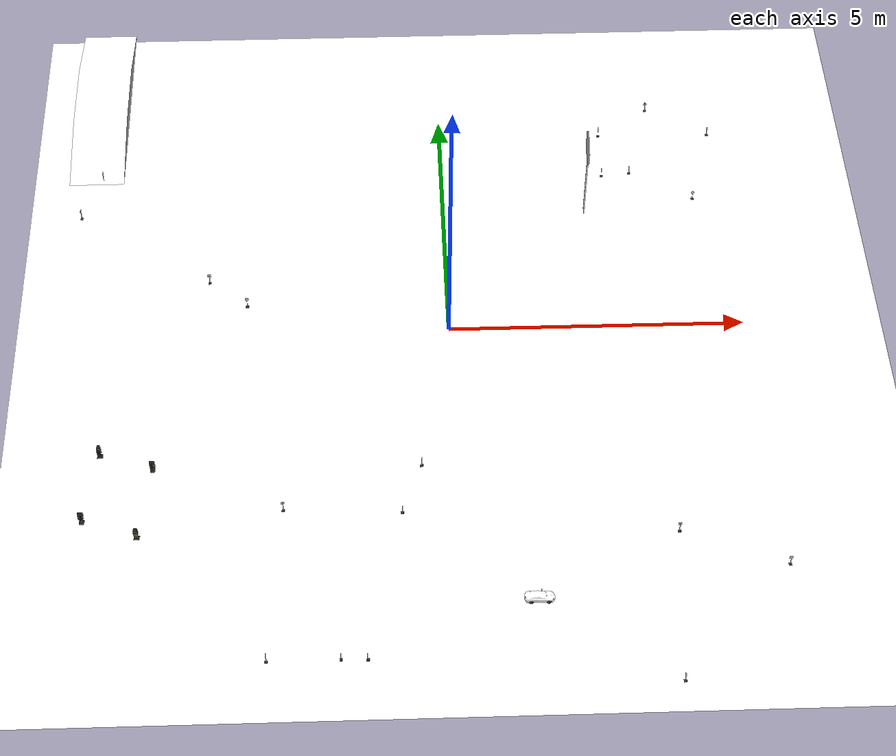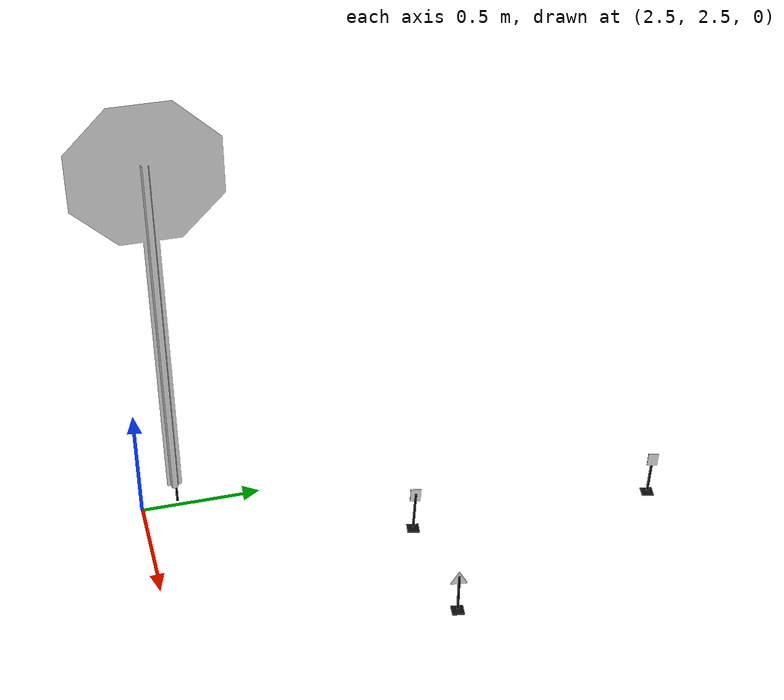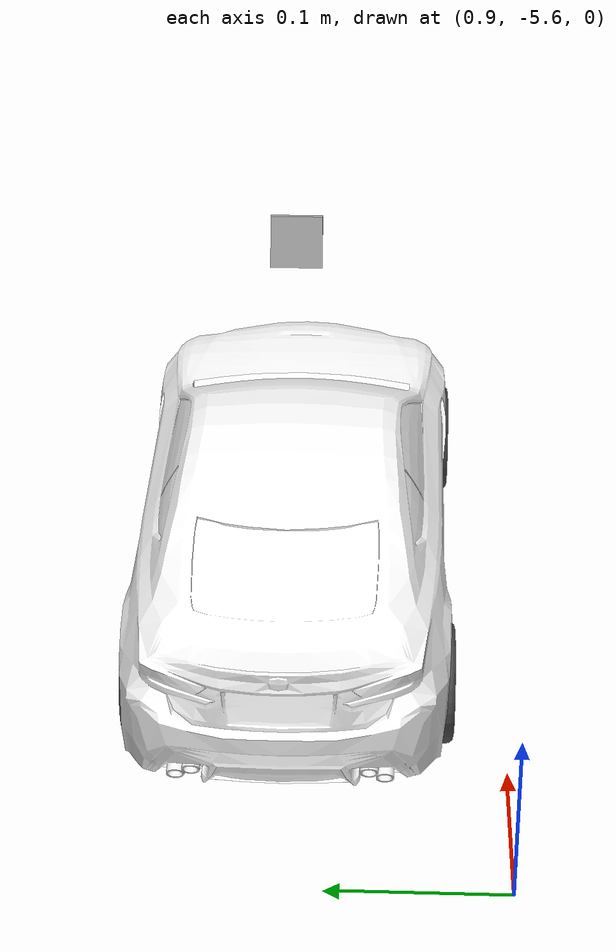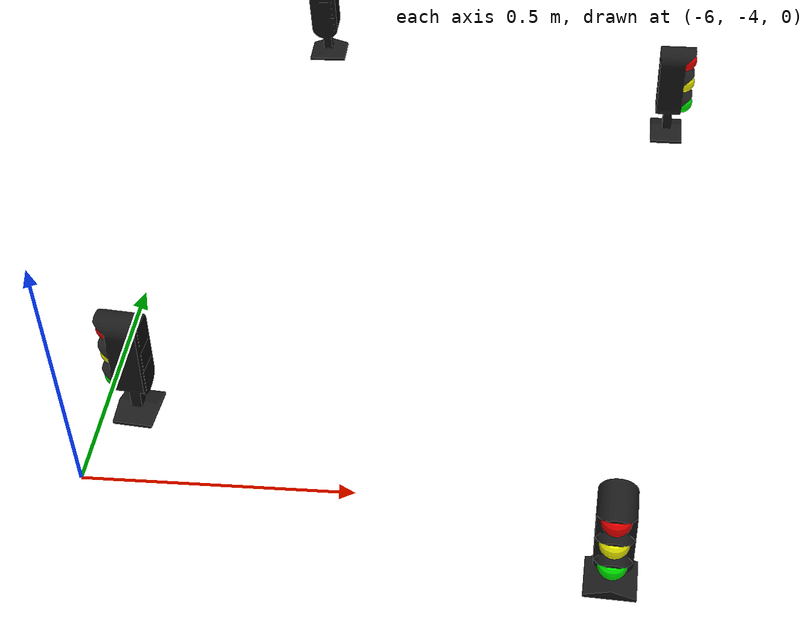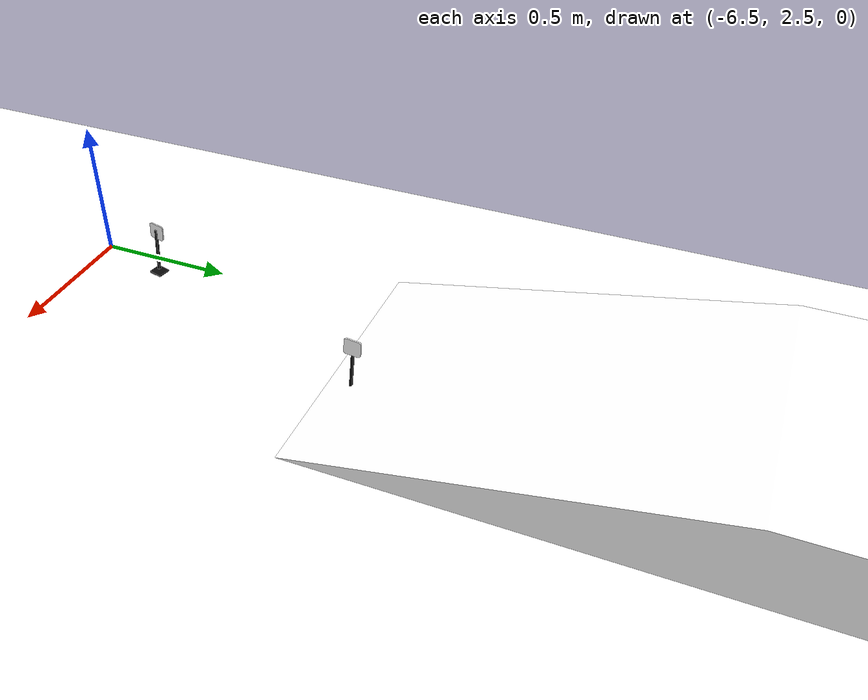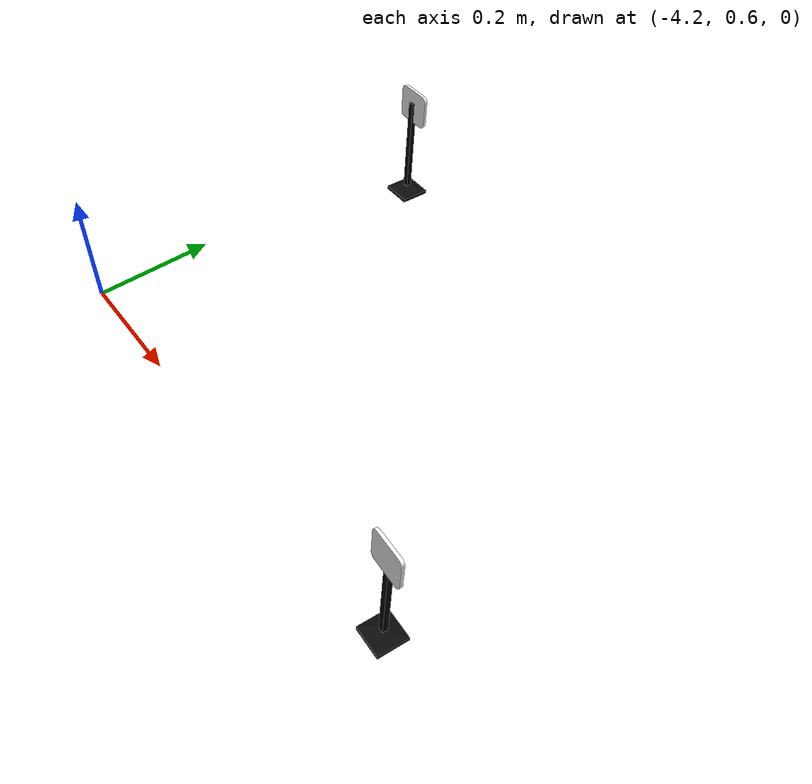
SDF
<sdf version='1.9'>
  <world name='bfmc_competition'>
    <plugin name='ignition::gazebo::systems::Physics' filename='ignition-gazebo-physics-system'/>
    <plugin name='ignition::gazebo::systems::UserCommands' filename='ignition-gazebo-user-commands-system'/>
    <plugin name='ignition::gazebo::systems::SceneBroadcaster' filename='ignition-gazebo-scene-broadcaster-system'/>
    <plugin name='ignition::gazebo::systems::Sensors' filename='ignition-gazebo-sensors-system'>
      <render_engine>ogre</render_engine>
    </plugin>
    <gravity>0 0 -9.8</gravity>
    <magnetic_field>6e-06 2.3e-05 -4.2e-05</magnetic_field>
    <atmosphere type='adiabatic'/>
    <physics type='ode'>
      <max_step_size>0.001</max_step_size>
      <real_time_factor>1</real_time_factor>
      <real_time_update_rate>1000</real_time_update_rate>
    </physics>
    <scene>
      <ambient>0.4 0.4 0.4 1</ambient>
      <background>0.7 0.7 0.7 1</background>
      <shadows>true</shadows>
    </scene>
    <include>
      <uri>file:///home/ros_dev/BFMC_workspace/files/simulation/models_pkg/track</uri>
      <name>track</name>
      <pose>0.016706 0 0 0 -0 0</pose>
    </include>
    <include>
      <uri>file:///home/ros_dev/BFMC_workspace/files/simulation/models_pkg/rcCar_assembly</uri>
      <name>automobile</name>
      <pose>1.19164 -5.47604 0.033 -0 -0 0.000191</pose>
    </include>
    <include>
      <uri>file:///home/ros_dev/BFMC_workspace/files/simulation/models_pkg/stop_sign</uri>
      <name>stop_sign_1</name>
      <pose>2.49908 2.64664 -0 0 -0 1.57</pose>
    </include>
    <include>
      <uri>file:///home/ros_dev/BFMC_workspace/files/simulation/models_pkg/parking_sign</uri>
      <name>parking_sign_1</name>
      <pose>-1.87467 -6.46909 0.079866 0 -0 0</pose>
    </include>
    <include>
      <uri>file:///home/ros_dev/BFMC_workspace/files/simulation/models_pkg/crosswalk_sign</uri>
      <name>crosswalk_sign_1</name>
      <pose>-4.08755 1.16427 0.096091 0.025359 -0.069592 -1.57459</pose>
    </include>
    <include>
      <uri>file:///home/ros_dev/BFMC_workspace/files/simulation/models_pkg/crosswalk_sign</uri>
      <name>crosswalk_sign_2</name>
      <pose>-3.43191 0.61495 0.081751 -0.017316 0.068193 1.51535</pose>
    </include>
    <include>
      <uri>file:///home/ros_dev/BFMC_workspace/files/simulation/models_pkg/crosswalk_sign</uri>
      <name>crosswalk_sign_3</name>
      <pose>-6.41862 2.78468 0.084666 -0.064323 -0.036734 -0.172223</pose>
    </include>
    <include>
      <uri>file:///home/ros_dev/BFMC_workspace/files/simulation/models_pkg/crosswalk_sign</uri>
      <name>crosswalk_sign_4</name>
      <pose>-6.08866 3.7206 0.076708 0.068678 0.027741 3.10427</pose>
    </include>
    <include>
      <uri>file:///home/ros_dev/BFMC_workspace/files/simulation/models_pkg/crosswalk_sign</uri>
      <name>crosswalk_sign_5</name>
      <pose>-0.887648 -3.79946 0.079984 0.007417 -0.025286 -0.003559</pose>
    </include>
    <include>
      <uri>file:///home/ros_dev/BFMC_workspace/files/simulation/models_pkg/crosswalk_sign</uri>
      <name>crosswalk_sign_6</name>
      <pose>-0.550989 -2.88027 0.079734 -0.002839 0.005615 -3.1276</pose>
    </include>
    <include>
      <uri>file:///home/ros_dev/BFMC_workspace/files/simulation/models_pkg/crosswalk_sign</uri>
      <name>crosswalk_sign_7</name>
      <pose>3.44538 -4.28555 0.090593 0.021297 -0.070939 -1.51674</pose>
    </include>
    <include>
      <uri>file:///home/ros_dev/BFMC_workspace/files/simulation/models_pkg/crosswalk_sign</uri>
      <name>crosswalk_sign_8</name>
      <pose>5.09387 -4.95671 0.070929 -0.028305 0.068449 1.52429</pose>
    </include>
    <include>
      <uri>file:///home/ros_dev/BFMC_workspace/files/simulation/models_pkg/crosswalk_sign</uri>
      <name>crosswalk_sign_9</name>
      <pose>-1.47445 -6.48127 0.079237 -0.012257 -0.027414 0.023757</pose>
    </include>
    <include>
      <uri>file:///home/ros_dev/BFMC_workspace/files/simulation/models_pkg/enter_highway_sign</uri>
      <name>enter_highway_sign_1</name>
      <pose>2.91761 4.6009 0.080586 -0.065208 -0.035139 -0.147615</pose>
    </include>
    <include>
      <uri>file:///home/ros_dev/BFMC_workspace/files/simulation/models_pkg/leave_highway_sign</uri>
      <name>leave_highway_sign_1</name>
      <pose>2.89639 3.57644 0.079478 0.065167 0.035217 2.99279</pose>
    </include>
    <include>
      <uri>file:///home/ros_dev/BFMC_workspace/files/simulation/models_pkg/oneway_sign</uri>
      <name>oneway_sign_1</name>
      <pose>-2.99632 -6.46929 0.077255 -0.069164 -0.026506 -0.019431</pose>
    </include>
    <include>
      <uri>file:///home/ros_dev/BFMC_workspace/files/simulation/models_pkg/prohibited_sign</uri>
      <name>prohibited_sign_1</name>
      <pose>-2.76805 -3.6967 0.085972 0.025423 -0.069569 -1.5755</pose>
    </include>
    <include>
      <uri>file:///home/ros_dev/BFMC_workspace/files/simulation/models_pkg/traffic_light</uri>
      <name>traffic_light_1</name>
      <pose>-4.82304 -2.84306 0.003361 0.045013 -0.034127 -0.056244</pose>
    </include>
    <include>
      <uri>file:///home/ros_dev/BFMC_workspace/files/simulation/models_pkg/traffic_light</uri>
      <name>traffic_light_2</name>
      <pose>-5.98097 -3.82495 0.006683 0.010053 -0.017608 3.06058</pose>
    </include>
    <include>
      <uri>file:///home/ros_dev/BFMC_workspace/files/simulation/models_pkg/traffic_light</uri>
      <name>traffic_light_3</name>
      <pose>-5.05814 -4.21128 0.007869 0.033136 0.045747 -1.64811</pose>
    </include>
    <include>
      <uri>file:///home/ros_dev/BFMC_workspace/files/simulation/models_pkg/traffic_light</uri>
      <name>traffic_light_4</name>
      <pose>-5.73069 -2.49314 0.007799 -0.033181 -0.030908 1.55798</pose>
    </include>
    <include>
      <uri>file:///home/ros_dev/BFMC_workspace/files/simulation/models_pkg/priority_sign</uri>
      <name>priority_sign_1</name>
      <pose>3.23408 -6.99215 0.083554 -0.070281 -0.023381 0.025343</pose>
    </include>
    <include>
      <uri>file:///home/ros_dev/BFMC_workspace/files/simulation/models_pkg/roundabout_sign</uri>
      <name>roundabout_sign_1</name>
      <pose>4.47623 2.95122 0.068534 -0.025944 0.069377 1.55859</pose>
    </include>
    <include>
      <uri>file:///home/ros_dev/BFMC_workspace/files/simulation/models_pkg/roundabout_sign</uri>
      <name>roundabout_sign_2</name>
      <pose>3.40253 3.62305 0.074259 -0.024515 -0.025748 -0.109547</pose>
    </include>
    <include>
      <uri>file:///home/ros_dev/BFMC_workspace/files/simulation/models_pkg/roundabout_sign</uri>
      <name>roundabout_sign_3</name>
      <pose>4.92274 4.57092 0.07548 0.071804 0.018165 -3.04296</pose>
    </include>
    <include>
      <uri>file:///home/ros_dev/BFMC_workspace/files/simulation/models_pkg/roundabout_sign</uri>
      <name>roundabout_sign_4</name>
      <pose>3.85139 5.25806 0.073845 0.02641 -0.069201 -1.58973</pose>
    </include>
    <include>
      <uri>file:///home/ros_dev/BFMC_workspace/files/simulation/models_pkg/ramp</uri>
      <name>ramp_1</name>
      <pose>-4.71511 5.63281 0 0 -0 0</pose>
    </include>
    <light name='sun' type='directional'>
      <pose>0 0 10 0 -0 0</pose>
      <cast_shadows>true</cast_shadows>
      <intensity>1</intensity>
      <direction>-0.5 0.1 -0.9</direction>
      <diffuse>1 1 1 1</diffuse>
      <specular>0.1 0.1 0.1 1</specular>
      <attenuation>
        <range>10</range>
        <linear>1</linear>
        <constant>1</constant>
        <quadratic>0</quadratic>
      </attenuation>
      <spot>
        <inner_angle>0</inner_angle>
        <outer_angle>0</outer_angle>
        <falloff>0</falloff>
      </spot>
    </light>
  </world>
</sdf>

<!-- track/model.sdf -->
<sdf version="1.8">
  <model name="track">
    <static>true</static>
    <link name="link">
      <collision name="collision">
        <geometry>
          <plane>
            <normal>0 0 1</normal>
	    <size>14.68000 14.99000</size>
          </plane>
        </geometry>
        <surface>
          <contact>
             <collide_bitmask>0xffff</collide_bitmask>
          </contact>
          <friction>
            <ode>
              <mu>1</mu>
              <mu2>1</mu2>
            </ode>
          </friction>
        </surface>
      </collision>

      <visual name="visual">
        <geometry>
          <plane>
            <normal>0 0 1</normal>
            <size>14.68 14.99</size>
          </plane>
        </geometry>
        <material>
          <diffuse>1 1 1 1</diffuse>
          <specular>0 0 0 1</specular>
          <pbr>
            <metal>
              <albedo_map>model://track/meshes/2024_Small.png</albedo_map>
            </metal>
          </pbr>
        </material>
      </visual>

    </link>
  </model>
</sdf>

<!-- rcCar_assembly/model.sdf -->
<sdf version="1.8">
  <model name='automobile'>
    <include><uri>model://chassis</uri></include>
    <include><uri>model://wheel_left</uri><pose>-0.152 0.081 0 0 0 0</pose><name>wheel_rear_left</name></include>
    <include><uri>model://wheel_right</uri><pose>-0.152 -0.081 0 0 0 0</pose><name>wheel_rear_right</name></include>
    <include><uri>model://steering_column</uri><pose>0.112 0.0725 0 0 0 0</pose><name>steer_left</name></include>
    <include><uri>model://steering_column</uri><pose>0.112 -0.0725 0 0 0 0</pose><name>steer_right</name></include>
    <include><uri>model://wheel_left</uri><pose>0.118 0.081 0 0 0 0</pose><name>wheel_front_left</name></include>
    <include><uri>model://wheel_right</uri><pose>0.118 -0.081 0 0 0 0</pose><name>wheel_front_right</name></include>
    <include><uri>model://camera</uri><pose>0 0 0.2 0 0.2617 0</pose><name>camera</name></include>
    <include><uri>model://car_body</uri><pose>-0.024 0.0 -0.028 0 0.0 0</pose><name>car_body</name></include>

    <joint name='joint_leftrear_rim' type='revolute'>
      <parent>chassis::link</parent>
      <child>wheel_rear_left::link_rim</child>
      <axis><xyz>0 0 -1</xyz><limit><lower>-1.7e+308</lower><upper>1.7e+308</upper></limit></axis>
    </joint>
    <joint name='joint_rightrear_rim' type='revolute'>
      <parent>chassis::link</parent>
      <child>wheel_rear_right::link_rim</child>
      <axis><xyz>0 0 -1</xyz><limit><lower>-1.7e+308</lower><upper>1.7e+308</upper></limit></axis>
    </joint>
    <joint name='joint_leftfront_steer' type='revolute'>
      <parent>chassis::link</parent>
      <child>steer_left::link_steer</child>
      <axis>
        <xyz>0 1 0</xyz>
        <limit>
          <lower>-0.52</lower>
          <upper>0.52</upper>
          <effort>1000.0</effort>
        </limit>
      </axis>
    </joint>
    <joint name='joint_rightfront_steer' type='revolute'>
      <parent>chassis::link</parent>
      <child>steer_right::link_steer</child>
      <axis>
        <xyz>0 1 0</xyz>
        <limit>
          <lower>-0.52</lower>
          <upper>0.52</upper>
          <effort>1000.0</effort>
        </limit>
      </axis>
    </joint>
    <joint name='joint_rightfront_rim' type='revolute'>
      <parent>steer_right::link_steer</parent>
      <child>wheel_front_right::link_rim</child>
      <axis><xyz>0 0 -1</xyz><limit><lower>-1.7e+308</lower><upper>1.7e+308</upper></limit></axis>
    </joint>
    <joint name='joint_leftfront_rim' type='revolute'>
      <parent>steer_left::link_steer</parent>
      <child>wheel_front_left::link_rim</child>
      <axis><xyz>0 0 -1</xyz><limit><lower>-1.7e+308</lower><upper>1.7e+308</upper></limit></axis>
    </joint>
    <joint name='joint_body' type='fixed'><parent>chassis::link</parent><child>car_body::link</child></joint>
    <joint name='joint_camera' type='fixed'><parent>chassis::link</parent><child>camera::link_camera</child></joint>

    <plugin filename="libignition-gazebo-ackermann-steering-system.so" name="ignition::gazebo::systems::AckermannSteering">
      <left_joint>joint_leftrear_rim</left_joint>
      <right_joint>joint_rightrear_rim</right_joint>
      <left_steering_joint>joint_leftfront_steer</left_steering_joint>
      <right_steering_joint>joint_rightfront_steer</right_steering_joint>
      <wheel_separation>0.162</wheel_separation>
      <wheel_base>0.26</wheel_base>
      <wheel_radius>0.0325</wheel_radius>
      <steering_limit>0.5</steering_limit>
      <topic>automobile/command</topic>
    </plugin>
    <plugin filename="libignition-gazebo-imu-system.so"
            name="ignition::gazebo::systems::Imu">
    </plugin>
  </model>
</sdf>

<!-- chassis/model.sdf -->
<sdf version="1.8">
  <model name='chassis'>
    <link name='link'>
      <inertial>
        <mass>0.26244</mass>
        <inertia>
          <ixx>0.00283444</ixx>
          <ixy>0</ixy>
          <ixz>0</ixz>
          <iyy>0.00039867</iyy>
          <iyz>0</iyz>
          <izz>0.00323293</izz>
        </inertia>
        <pose frame=''>0 0 0 0 -0 0</pose>
      </inertial>
      <pose frame=''>0 0 0 0 0 1.5708</pose>
      <gravity>1</gravity>
      <kinematic>0</kinematic>
      <enable_wind>0</enable_wind>
      <visual name='visual'>
        <pose frame=''>0 0 -0.0065 0 0 -1.57079</pose>
        <geometry>
          <mesh>
            <uri>model://chassis/meshes/chassisV5.dae</uri>
            <scale>1 1 1</scale>
          </mesh>
        </geometry>
        <material>
          <lighting>1</lighting>
          <shader type='vertex'>
            <normal_map>__default__</normal_map>
          </shader>
          <ambient>0.6 0.6 0.6 1</ambient>
          <diffuse>0.85 0.85 0.85 1</diffuse>
          <specular>0.6 0.6 0.6 1</specular>
          <emissive>0 0 0 1</emissive>
        </material>
        <transparency>0</transparency>
        <cast_shadows>1</cast_shadows>
      </visual>
      <collision name='collision'>
        <laser_retro>0</laser_retro>
        <max_contacts>10</max_contacts>
        <pose frame=''>0 0 0 0 -0 0</pose>
        <geometry>
          <box>
            <size>0.135 0.36 0.002</size>
          </box>
        </geometry>
        <surface>
          <friction>
            <ode>
              <mu>1</mu>
              <mu2>1</mu2>
              <fdir1>0 0 0</fdir1>
              <slip1>0</slip1>
              <slip2>0</slip2>
            </ode>
            <torsional>
              <coefficient>1</coefficient>
              <patch_radius>0</patch_radius>
              <surface_radius>0</surface_radius>
              <use_patch_radius>1</use_patch_radius>
              <ode>
                <slip>0</slip>
              </ode>
            </torsional>
          </friction>
          <bounce>
            <restitution_coefficient>0</restitution_coefficient>
            <threshold>1e+06</threshold>
          </bounce>
          <contact>
            <collide_without_contact>0</collide_without_contact>
            <collide_without_contact_bitmask>1</collide_without_contact_bitmask>
            <collide_bitmask>1</collide_bitmask>
            <ode>
              <soft_cfm>0</soft_cfm>
              <soft_erp>0.2</soft_erp>
              <kp>1e+13</kp>
              <kd>1</kd>
              <max_vel>0.01</max_vel>
              <min_depth>0</min_depth>
            </ode>
            <bullet>
              <split_impulse>1</split_impulse>
              <split_impulse_penetration_threshold>-0.01</split_impulse_penetration_threshold>
              <soft_cfm>0</soft_cfm>
              <soft_erp>0.2</soft_erp>
              <kp>1e+13</kp>
              <kd>1</kd>
            </bullet>
          </contact>
        </surface>
      </collision>

      <sensor name="imu_sensor" type="imu">
        <always_on>1</always_on>
        <update_rate>100</update_rate>
        <visualize>true</visualize>
        <topic>automobile/IMU</topic>
      </sensor>

    </link>
  </model>
</sdf>

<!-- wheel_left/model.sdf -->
<sdf version="1.8">
  <model name='wheel_left'>

    <link name='link_rim'>
      <inertial>
        <mass>0.038</mass>
        <inertia>
          <ixx>0.00001283</ixx>
          <ixy>0</ixy>
          <ixz>0</ixz>
          <iyy>0.00001283</iyy>
          <iyz>0</iyz>
          <izz>0.00002069</izz>
        </inertia>
        <pose frame=''>0 0 0 0 -0 0</pose>
      </inertial>
      <pose frame=''>0.0 0.0 0 1.5708 0 0</pose>
      <gravity>1</gravity>
      <kinematic>0</kinematic>
      <enable_wind>0</enable_wind>
      <visual name='visual'>
       <pose frame=''>0 0 0 -1.5708 0 0</pose>
       <geometry>
          <mesh>
            <uri>model://wheel_left/meshes/rim.dae</uri>
            <scale>1 1 1</scale>
          </mesh>
        </geometry>
        <material>
          <lighting>1</lighting>
          <shader type='vertex'>
            <normal_map>__default__</normal_map>
          </shader>
          <ambient>0.2 0.2 0.2 1</ambient>
          <diffuse>0.3 0.3 0.3 1</diffuse>
          <specular>0.5 0.5 0.5 1</specular>
          <emissive>0.0 0.0 0.0 0.0</emissive>
        </material>
        <transparency>0</transparency>
        <cast_shadows>1</cast_shadows>
      </visual>
      <collision name='collision'>
        <laser_retro>0</laser_retro>
        <max_contacts>10</max_contacts>
        <pose frame=''>0 0 0 0 -0 0</pose>
        <geometry>
          <cylinder>
            <radius>0.033000</radius>
            <length>0.028000</length>
          </cylinder>
        </geometry>
        <surface>
          <friction>
            <ode>
              <mu>0.7</mu>
              <mu2>0.7</mu2>
              <fdir1>0 0 0</fdir1>
              <slip1>0</slip1>
              <slip2>0</slip2>
            </ode>
            <torsional>
              <coefficient>1</coefficient>
              <patch_radius>0</patch_radius>
              <surface_radius>0</surface_radius>
              <use_patch_radius>1</use_patch_radius>
              <ode>
                <slip>0</slip>
              </ode>
            </torsional>
          </friction>
          <bounce>
            <restitution_coefficient>0</restitution_coefficient>
            <threshold>1e+06</threshold>
          </bounce>
          <contact>
            <collide_without_contact>0</collide_without_contact>
            <collide_without_contact_bitmask>1</collide_without_contact_bitmask>
            <collide_bitmask>1</collide_bitmask>
            <ode>
              <soft_cfm>0</soft_cfm>
              <soft_erp>0.2</soft_erp>
              <kp>1e+07</kp>
              <kd>1</kd>
              <max_vel>0.01</max_vel>
              <min_depth>0</min_depth>
            </ode>
            <bullet>
              <split_impulse>1</split_impulse>
              <split_impulse_penetration_threshold>-0.01</split_impulse_penetration_threshold>
              <soft_cfm>0</soft_cfm>
              <soft_erp>0.2</soft_erp>
              <kp>1e+07</kp>
              <kd>1</kd>
            </bullet>
          </contact>
        </surface>
      </collision>
    </link>

  </model>
</sdf>

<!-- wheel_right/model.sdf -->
<sdf version="1.8">
  <model name='wheel_right'>

    <link name='link_rim'>
      <inertial>
        <mass>0.038</mass>
        <inertia>
          <ixx>0.00001283</ixx>
          <ixy>0</ixy>
          <ixz>0</ixz>
          <iyy>0.00001283</iyy>
          <iyz>0</iyz>
          <izz>0.00002069</izz>
        </inertia>
        <pose frame=''>0 0 0 0 -0 0</pose>
      </inertial>
      <pose frame=''>0.0 0.0 0 1.5708 0 0</pose>
      <gravity>1</gravity>
      <kinematic>0</kinematic>
      <enable_wind>0</enable_wind>
      <visual name='visual'>
       <pose frame=''>0 0 0 -1.5708 0 0</pose>
       <geometry>
          <mesh>
            <uri>model://wheel_right/meshes/rim.dae</uri>
            <scale>1 1 1</scale>
          </mesh>
        </geometry>
        <material>
          <lighting>1</lighting>
          <shader type='vertex'>
            <normal_map>__default__</normal_map>
          </shader>
          <ambient>0.2 0.2 0.2 1</ambient>
          <diffuse>0.3 0.3 0.3 1</diffuse>
          <specular>0.5 0.5 0.5 1</specular>
          <emissive>0.0 0.0 0.0 0.0</emissive>
        </material>
        <transparency>0</transparency>
        <cast_shadows>1</cast_shadows>
      </visual>
      <collision name='collision'>
        <laser_retro>0</laser_retro>
        <max_contacts>10</max_contacts>
        <pose frame=''>0 0 0 0 -0 0</pose>
        <geometry>
          <cylinder>
            <radius>0.033000</radius>
            <length>0.028000</length>
          </cylinder>
        </geometry>
        <surface>
          <friction>
            <ode>
              <mu>0.7</mu>
              <mu2>0.7</mu2>
              <fdir1>0 0 0</fdir1>
              <slip1>0</slip1>
              <slip2>0</slip2>
            </ode>
            <torsional>
              <coefficient>1</coefficient>
              <patch_radius>0</patch_radius>
              <surface_radius>0</surface_radius>
              <use_patch_radius>1</use_patch_radius>
              <ode>
                <slip>0</slip>
              </ode>
            </torsional>
          </friction>
          <bounce>
            <restitution_coefficient>0</restitution_coefficient>
            <threshold>1e+06</threshold>
          </bounce>
          <contact>
            <collide_without_contact>0</collide_without_contact>
            <collide_without_contact_bitmask>1</collide_without_contact_bitmask>
            <collide_bitmask>1</collide_bitmask>
            <ode>
              <soft_cfm>0</soft_cfm>
              <soft_erp>0.2</soft_erp>
              <kp>1e+07</kp>
              <kd>1</kd>
              <max_vel>0.01</max_vel>
              <min_depth>0</min_depth>
            </ode>
            <bullet>
              <split_impulse>1</split_impulse>
              <split_impulse_penetration_threshold>-0.01</split_impulse_penetration_threshold>
              <soft_cfm>0</soft_cfm>
              <soft_erp>0.2</soft_erp>
              <kp>1e+07</kp>
              <kd>1</kd>
            </bullet>
          </contact>
        </surface>
      </collision>
    </link>

  </model>
</sdf>

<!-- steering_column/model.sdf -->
<sdf version="1.8">
  <model name='steering_column'>
    <link name='link_steer'>
      <inertial>
        <mass>0.001</mass>
        <inertia>
          <ixx>0.00014583</ixx>
          <ixy>0</ixy>
          <ixz>0</ixz>
          <iyy>0.00014583</iyy>
          <iyz>0</iyz>
          <izz>0.000125</izz>
        </inertia>
        <pose frame=''>0 0 0 0 -0 0</pose>
      </inertial>
      <pose frame=''>0 0 0 1.5708 0 0</pose>
      <gravity>1</gravity>
      <self_collide>0</self_collide>
      <kinematic>0</kinematic>
      <enable_wind>0</enable_wind>
      <visual name='visual'>
        <pose frame=''>0 0 0 0 -0 0</pose>
        <geometry>
          <cylinder>
            <radius>0.001</radius>
            <length>0.01</length>
          </cylinder>
        </geometry>
        <material>
          <lighting>1</lighting>
          <script>
            <uri>file://media/materials/scripts/gazebo.material</uri>
            <name>Gazebo/Grey</name>
          </script>
          <shader type='vertex'>
            <normal_map>__default__</normal_map>
          </shader>
          <ambient>0.3 0.3 0.3 1</ambient>
          <diffuse>0.7 0.7 0.7 1</diffuse>
          <specular>0.01 0.01 0.01 1</specular>
          <emissive>0 0 0 1</emissive>
        </material>
        <transparency>0</transparency>
        <cast_shadows>1</cast_shadows>
      </visual>
      <collision name='collision'>
        <laser_retro>0</laser_retro>
        <max_contacts>10</max_contacts>
        <pose frame=''>0 0 0 0 -0 0</pose>
        <geometry>
          <cylinder>
            <radius>0.001</radius>
            <length>0.01</length>
          </cylinder>
        </geometry>
        <surface>
          <friction>
            <ode>
              <mu>1</mu>
              <mu2>1</mu2>
              <fdir1>0 0 0</fdir1>
              <slip1>0</slip1>
              <slip2>0</slip2>
            </ode>
            <torsional>
              <coefficient>1</coefficient>
              <patch_radius>0</patch_radius>
              <surface_radius>0</surface_radius>
              <use_patch_radius>1</use_patch_radius>
              <ode>
                <slip>0</slip>
              </ode>
            </torsional>
          </friction>
          <bounce>
            <restitution_coefficient>0</restitution_coefficient>
            <threshold>1e+06</threshold>
          </bounce>
          <contact>
            <collide_without_contact>0</collide_without_contact>
            <collide_without_contact_bitmask>1</collide_without_contact_bitmask>
            <collide_bitmask>1</collide_bitmask>
            <ode>
              <soft_cfm>0</soft_cfm>
              <soft_erp>0.2</soft_erp>
              <kp>1e+13</kp>
              <kd>1</kd>
              <max_vel>0.01</max_vel>
              <min_depth>0</min_depth>
            </ode>
            <bullet>
              <split_impulse>1</split_impulse>
              <split_impulse_penetration_threshold>-0.01</split_impulse_penetration_threshold>
              <soft_cfm>0</soft_cfm>
              <soft_erp>0.2</soft_erp>
              <kp>1e+13</kp>
              <kd>1</kd>
            </bullet>
          </contact>
        </surface>
      </collision>
    </link>

  </model>
</sdf>

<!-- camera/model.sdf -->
<sdf version="1.8">
  <model name='camera'>
    <link name='link_camera'>
      <inertial>
        <mass>0.0052875</mass>
        <inertia>
          <ixx>4.1e-07</ixx>
          <ixy>0</ixy>
          <ixz>0</ixz>
          <iyy>7.9e-07</iyy>
          <iyz>0</iyz>
          <izz>4.1e-07</izz>
        </inertia>
      </inertial>
      <visual name='visual'>
        <geometry>
          <box>
            <size>0.005 0.03 0.03</size>
          </box>
        </geometry>
        <material>
          <ambient>0.3 0.3 0.3 1</ambient>
          <diffuse>0.7 0.7 0.7 1</diffuse>
          <specular>0.01 0.01 0.01 1</specular>
        </material>
      </visual>
      <collision name='collision'>
        <geometry>
          <box>
            <size>0.005 0.03 0.03</size>
          </box>
        </geometry>
      </collision>

      <sensor type="camera" name="camera1">
        <update_rate>30.0</update_rate>
        <visualize>true</visualize>
        <always_on>1</always_on>
        <topic>automobile/camera/image_raw</topic>
        <gz_frame_id>link_camera</gz_frame_id>
        <camera name="head">
          <horizontal_fov>1.085594795</horizontal_fov>
          <image>
            <width>640</width>
            <height>480</height>
            <format>R8G8B8</format>
          </image>
          <clip>
            <near>0.02</near>
            <far>100</far>
          </clip>
        </camera>
      </sensor>
    </link>
  </model>
</sdf>

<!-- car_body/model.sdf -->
<sdf version="1.8">
  <model name='body'>
    <link name='link'>
      <inertial>
        <mass>1</mass>
        <inertia>
          <ixx>0.166667</ixx>
          <ixy>0</ixy>
          <ixz>0</ixz>
          <iyy>0.166667</iyy>
          <iyz>0</iyz>
          <izz>0.166667</izz>
        </inertia>
      </inertial>
      <pose frame=''>0 -0 0 0 -0 0</pose>
      <visual name='visual'>
        <pose frame=''>0 0 0 0 -0 0</pose>
        <geometry>
          <mesh>
            <uri>model://car_body/meshes/CarBody.dae</uri>
            <scale>1 1 1</scale>
          </mesh>
        </geometry>
        <material>
          <diffuse>1 1 1 1</diffuse>
          <specular>0.5 0.5 0.5 1</specular>
          <pbr>
            <metal>
              <albedo_map>model://car_body/meshes/Colors.png</albedo_map>
            </metal>
          </pbr>
        </material>
        <transparency>0</transparency>
        <cast_shadows>1</cast_shadows>
      </visual>
    </link>
    <static>0</static>
    <allow_auto_disable>1</allow_auto_disable>
  </model>
</sdf>

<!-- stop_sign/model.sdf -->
<sdf version="1.8">
  <model name='stop_sign'>
    <static>1</static>
    <link name='sign_leg'>
      <inertial>
        <mass>0.5</mass>
        <inertia>
          <ixx>0.166667</ixx>
          <ixy>0</ixy>
          <ixz>0</ixz>
          <iyy>0.166667</iyy>
          <iyz>0</iyz>
          <izz>0.166667</izz>
        </inertia>
	<pose>0 0 -0.078998 0.0 0.0 0.0 </pose>
        <pose frame=''>0 0 0 0 -0 0</pose>
      </inertial>
      <pose frame=''>0.002193 -0.000682 -0.07606 0 -0 0</pose>
      <gravity>1</gravity>
      <self_collide>1</self_collide>
      <kinematic>0</kinematic>
      <enable_wind>1</enable_wind>
      <visual name='visual'>
        <pose frame=''>0 0 0 0 -0 0</pose>
        <geometry>
          <mesh>
            <uri>model://subassembly/meshes/sign_leg.dae</uri>
            <scale>1 1 1</scale>
          </mesh>
        </geometry>
        <transparency>0</transparency>
        <cast_shadows>1</cast_shadows>
      </visual>
      <collision name='collision'>
        <laser_retro>0</laser_retro>
        <max_contacts>10</max_contacts>
        <pose frame=''>0 0 0 0 -0 0</pose>
        <geometry>
          <mesh>
            <uri>model://subassembly/meshes/sign_leg.dae</uri>
            <scale>1 1 1</scale>
          </mesh>
        </geometry>
        <surface>
          <friction>
            <ode>
              <mu>0.46</mu>
              <mu2>1</mu2>
              <fdir1>0 0 0</fdir1>
              <slip1>0</slip1>
              <slip2>0</slip2>
            </ode>
            <torsional>
              <coefficient>1</coefficient>
              <patch_radius>0</patch_radius>
              <surface_radius>0</surface_radius>
              <use_patch_radius>1</use_patch_radius>
              <ode>
                <slip>0</slip>
              </ode>
            </torsional>
          </friction>
          <bounce>
            <restitution_coefficient>0</restitution_coefficient>
            <threshold>1e+06</threshold>
          </bounce>
          <contact>
            <collide_without_contact>0</collide_without_contact>
            <collide_without_contact_bitmask>1</collide_without_contact_bitmask>
            <collide_bitmask>1</collide_bitmask>
            <ode>
              <soft_cfm>0</soft_cfm>
              <soft_erp>0.2</soft_erp>
              <kp>1e+13</kp>
              <kd>1</kd>
              <max_vel>0.01</max_vel>
              <min_depth>0</min_depth>
            </ode>
            <bullet>
              <split_impulse>1</split_impulse>
              <split_impulse_penetration_threshold>-0.01</split_impulse_penetration_threshold>
              <soft_cfm>0</soft_cfm>
              <soft_erp>0.2</soft_erp>
              <kp>1e+13</kp>
              <kd>1</kd>
            </bullet>
          </contact>
        </surface>
      </collision>
    </link>
    <link name='octagonal_support'>
      <inertial>
        <mass>0.022</mass>
        <inertia>
          <ixx>0.166667</ixx>
          <ixy>0</ixy>
          <ixz>0</ixz>
          <iyy>0.166667</iyy>
          <iyz>0</iyz>
          <izz>0.166667</izz>
        </inertia>
        <pose frame=''>0 0 0 0 -0 0</pose>
      </inertial>
      <pose frame=''>-0.002193 0.000682 0.09894 0 0 3.141592</pose>
      <gravity>1</gravity>
      <self_collide>1</self_collide>
      <kinematic>0</kinematic>
      <enable_wind>1</enable_wind>
      <visual name='visual'>
        <pose frame=''>0 0 0 0 -0 0</pose>
        <geometry>
          <mesh>
            <uri>model://stop_sign/meshes/stop_sign.dae</uri>
            <scale>1 1 1</scale>
          </mesh>
        </geometry>
        <material>
          <diffuse>1 1 1 1</diffuse>
          <specular>0.2 0.2 0.2 1</specular>
          <pbr>
            <metal>
              <albedo_map>model://stop_sign/meshes/stop_sign.png</albedo_map>
            </metal>
          </pbr>
        </material>
        <transparency>0</transparency>
        <cast_shadows>1</cast_shadows>
      </visual>
      <collision name='collision'>
        <laser_retro>0</laser_retro>
        <max_contacts>10</max_contacts>
        <pose frame=''>0 0 0 0 -0 0</pose>
        <geometry>
          <mesh>
            <uri>model://stop_sign/meshes/stop_sign.dae</uri>
            <scale>1 1 1</scale>
          </mesh>
        </geometry>
        <surface>
          <friction>
            <ode>
              <mu>0.46</mu>
              <mu2>1</mu2>
              <fdir1>0 0 0</fdir1>
              <slip1>0</slip1>
              <slip2>0</slip2>
            </ode>
            <torsional>
              <coefficient>1</coefficient>
              <patch_radius>0</patch_radius>
              <surface_radius>0</surface_radius>
              <use_patch_radius>1</use_patch_radius>
              <ode>
                <slip>0</slip>
              </ode>
            </torsional>
          </friction>
          <bounce>
            <restitution_coefficient>0</restitution_coefficient>
            <threshold>1e+06</threshold>
          </bounce>
          <contact>
            <collide_without_contact>0</collide_without_contact>
            <collide_without_contact_bitmask>1</collide_without_contact_bitmask>
            <collide_bitmask>1</collide_bitmask>
            <ode>
              <soft_cfm>0</soft_cfm>
              <soft_erp>0.2</soft_erp>
              <kp>1e+13</kp>
              <kd>1</kd>
              <max_vel>0.01</max_vel>
              <min_depth>0</min_depth>
            </ode>
            <bullet>
              <split_impulse>1</split_impulse>
              <split_impulse_penetration_threshold>-0.01</split_impulse_penetration_threshold>
              <soft_cfm>0</soft_cfm>
              <soft_erp>0.2</soft_erp>
              <kp>1e+13</kp>
              <kd>1</kd>
            </bullet>
          </contact>
        </surface>
      </collision>
    </link>
    <joint name='support_to_leg_joint' type='fixed'>
      <parent>sign_leg</parent>
      <child>octagonal_support</child>
      <pose frame=''>0 0 0 0 -0 0</pose>
      <physics>
        <ode>
          <limit>
            <cfm>0</cfm>
            <erp>0.2</erp>
          </limit>
          <suspension>
            <cfm>0</cfm>
            <erp>0.2</erp>
          </suspension>
        </ode>
      </physics>
    </joint>
    <static>1</static>
    <allow_auto_disable>1</allow_auto_disable>

  </model>
</sdf>

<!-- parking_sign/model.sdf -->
<sdf version="1.8">
  <model name='parking_sign'>
    <static>1</static>
    <link name='sign_leg'>
      <inertial>
        <mass>0.5</mass>
        <inertia>
          <ixx>0.166667</ixx>
          <ixy>0</ixy>
          <ixz>0</ixz>
          <iyy>0.166667</iyy>
          <iyz>0</iyz>
          <izz>0.166667</izz>
        </inertia>
	<pose>0 0 -0.078998 0.0 0.0 0.0 </pose>
        <pose frame=''>0 0 0 0 -0 0</pose>
      </inertial>
      <pose frame=''>0.002193 -0.000682 -0.07606 0 -0 0</pose>
      <gravity>1</gravity>
      <self_collide>1</self_collide>
      <kinematic>0</kinematic>
      <enable_wind>1</enable_wind>
      <visual name='visual'>
        <pose frame=''>0 0 0 0 -0 0</pose>
        <geometry>
          <mesh>
            <uri>model://subassembly/meshes/sign_leg.dae</uri>
            <scale>1 1 1</scale>
          </mesh>
        </geometry>
        <transparency>0</transparency>
        <cast_shadows>1</cast_shadows>
      </visual>
      <collision name='collision'>
        <laser_retro>0</laser_retro>
        <max_contacts>10</max_contacts>
        <pose frame=''>0 0 0 0 -0 0</pose>
        <geometry>
          <mesh>
            <uri>model://subassembly/meshes/sign_leg.dae</uri>
            <scale>1 1 1</scale>
          </mesh>
        </geometry>
        <surface>
          <friction>
            <ode>
              <mu>0.46</mu>
              <mu2>1</mu2>
              <fdir1>0 0 0</fdir1>
              <slip1>0</slip1>
              <slip2>0</slip2>
            </ode>
            <torsional>
              <coefficient>1</coefficient>
              <patch_radius>0</patch_radius>
              <surface_radius>0</surface_radius>
              <use_patch_radius>1</use_patch_radius>
              <ode>
                <slip>0</slip>
              </ode>
            </torsional>
          </friction>
          <bounce>
            <restitution_coefficient>0</restitution_coefficient>
            <threshold>1e+06</threshold>
          </bounce>
          <contact>
            <collide_without_contact>0</collide_without_contact>
            <collide_without_contact_bitmask>1</collide_without_contact_bitmask>
            <collide_bitmask>1</collide_bitmask>
            <ode>
              <soft_cfm>0</soft_cfm>
              <soft_erp>0.2</soft_erp>
              <kp>1e+13</kp>
              <kd>1</kd>
              <max_vel>0.01</max_vel>
              <min_depth>0</min_depth>
            </ode>
            <bullet>
              <split_impulse>1</split_impulse>
              <split_impulse_penetration_threshold>-0.01</split_impulse_penetration_threshold>
              <soft_cfm>0</soft_cfm>
              <soft_erp>0.2</soft_erp>
              <kp>1e+13</kp>
              <kd>1</kd>
            </bullet>
          </contact>
        </surface>
      </collision>
    </link>
    <link name='rectangular_support'>
      <inertial>
        <mass>0.022</mass>
        <inertia>
          <ixx>0.166667</ixx>
          <ixy>0</ixy>
          <ixz>0</ixz>
          <iyy>0.166667</iyy>
          <iyz>0</iyz>
          <izz>0.166667</izz>
        </inertia>
        <pose frame=''>0 0 0 0 -0 0</pose>
      </inertial>
      <pose frame=''>-0.002193 0.000682 0.09894 0 0 3.141592</pose>
      <gravity>1</gravity>
      <self_collide>1</self_collide>
      <kinematic>0</kinematic>
      <enable_wind>1</enable_wind>
      <visual name='visual'>
        <pose frame=''>0 0 0 0 -0 0</pose>
        <geometry>
          <mesh>
            <uri>model://parking_sign/meshes/parking_sign.dae</uri>
            <scale>10 10 10</scale>
          </mesh>
        </geometry>
        <material>
          <diffuse>1 1 1 1</diffuse>
          <specular>0.2 0.2 0.2 1</specular>
          <pbr>
            <metal>
              <albedo_map>model://parking_sign/meshes/parking_sign.png</albedo_map>
            </metal>
          </pbr>
        </material>
        <transparency>0</transparency>
        <cast_shadows>1</cast_shadows>
      </visual>
      <collision name='collision'>
        <laser_retro>0</laser_retro>
        <max_contacts>10</max_contacts>
        <pose frame=''>0 0 0 0 -0 0</pose>
        <geometry>
          <mesh>
            <uri>model://parking_sign/meshes/parking_sign.dae</uri>
            <scale>10 10 10</scale>
          </mesh>
        </geometry>
        <surface>
          <friction>
            <ode>
              <mu>0.46</mu>
              <mu2>1</mu2>
              <fdir1>0 0 0</fdir1>
              <slip1>0</slip1>
              <slip2>0</slip2>
            </ode>
            <torsional>
              <coefficient>1</coefficient>
              <patch_radius>0</patch_radius>
              <surface_radius>0</surface_radius>
              <use_patch_radius>1</use_patch_radius>
              <ode>
                <slip>0</slip>
              </ode>
            </torsional>
          </friction>
          <bounce>
            <restitution_coefficient>0</restitution_coefficient>
            <threshold>1e+06</threshold>
          </bounce>
          <contact>
            <collide_without_contact>0</collide_without_contact>
            <collide_without_contact_bitmask>1</collide_without_contact_bitmask>
            <collide_bitmask>1</collide_bitmask>
            <ode>
              <soft_cfm>0</soft_cfm>
              <soft_erp>0.2</soft_erp>
              <kp>1e+13</kp>
              <kd>1</kd>
              <max_vel>0.01</max_vel>
              <min_depth>0</min_depth>
            </ode>
            <bullet>
              <split_impulse>1</split_impulse>
              <split_impulse_penetration_threshold>-0.01</split_impulse_penetration_threshold>
              <soft_cfm>0</soft_cfm>
              <soft_erp>0.2</soft_erp>
              <kp>1e+13</kp>
              <kd>1</kd>
            </bullet>
          </contact>
        </surface>
      </collision>
    </link>
    <joint name='support_to_leg_joint' type='fixed'>
      <parent>sign_leg</parent> <child>rectangular_support</child> <pose frame=''>0 0 0 0 -0 0</pose>
      <physics>
        <ode>
          <limit>
            <cfm>0</cfm>
            <erp>0.2</erp>
          </limit>
          <suspension>
            <cfm>0</cfm>
            <erp>0.2</erp>
          </suspension>
        </ode>
      </physics>
    </joint>
    <static>1</static>
    <allow_auto_disable>1</allow_auto_disable>
  </model>
</sdf>

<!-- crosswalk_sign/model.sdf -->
<sdf version="1.8">
  <model name='crosswalk_sign'>
    <static>1</static>
    <link name='sign_leg'>
      <inertial>
        <mass>0.5</mass>
        <inertia>
          <ixx>0.166667</ixx>
          <ixy>0</ixy>
          <ixz>0</ixz>
          <iyy>0.166667</iyy>
          <iyz>0</iyz>
          <izz>0.166667</izz>
        </inertia>
	<pose>0 0 -0.078998 0.0 0.0 0.0 </pose>
        <pose frame=''>0 0 0 0 -0 0</pose>
      </inertial>
      <pose frame=''>0.002193 -0.000682 -0.07606 0 -0 0</pose>
      <gravity>1</gravity>
      <self_collide>1</self_collide>
      <kinematic>0</kinematic>
      <enable_wind>1</enable_wind>
      <visual name='visual'>
        <pose frame=''>0 0 0 0 -0 0</pose>
        <geometry>
          <mesh>
            <uri>model://subassembly/meshes/sign_leg.dae</uri>
            <scale>1 1 1</scale>
          </mesh>
        </geometry>
        <transparency>0</transparency>
        <cast_shadows>1</cast_shadows>
      </visual>
      <collision name='collision'>
        <laser_retro>0</laser_retro>
        <max_contacts>10</max_contacts>
        <pose frame=''>0 0 0 0 -0 0</pose>
        <geometry>
          <mesh>
            <uri>model://subassembly/meshes/sign_leg.dae</uri>
            <scale>1 1 1</scale>
          </mesh>
        </geometry>
        <surface>
          <friction>
            <ode>
              <mu>0.46</mu>
              <mu2>1</mu2>
              <fdir1>0 0 0</fdir1>
              <slip1>0</slip1>
              <slip2>0</slip2>
            </ode>
            <torsional>
              <coefficient>1</coefficient>
              <patch_radius>0</patch_radius>
              <surface_radius>0</surface_radius>
              <use_patch_radius>1</use_patch_radius>
              <ode>
                <slip>0</slip>
              </ode>
            </torsional>
          </friction>
          <bounce>
            <restitution_coefficient>0</restitution_coefficient>
            <threshold>1e+06</threshold>
          </bounce>
          <contact>
            <collide_without_contact>0</collide_without_contact>
            <collide_without_contact_bitmask>1</collide_without_contact_bitmask>
            <collide_bitmask>1</collide_bitmask>
            <ode>
              <soft_cfm>0</soft_cfm>
              <soft_erp>0.2</soft_erp>
              <kp>1e+13</kp>
              <kd>1</kd>
              <max_vel>0.01</max_vel>
              <min_depth>0</min_depth>
            </ode>
            <bullet>
              <split_impulse>1</split_impulse>
              <split_impulse_penetration_threshold>-0.01</split_impulse_penetration_threshold>
              <soft_cfm>0</soft_cfm>
              <soft_erp>0.2</soft_erp>
              <kp>1e+13</kp>
              <kd>1</kd>
            </bullet>
          </contact>
        </surface>
      </collision>
    </link>
    <link name='rectangular_support'>
      <inertial>
        <mass>0.022</mass>
        <inertia>
          <ixx>0.166667</ixx>
          <ixy>0</ixy>
          <ixz>0</ixz>
          <iyy>0.166667</iyy>
          <iyz>0</iyz>
          <izz>0.166667</izz>
        </inertia>
        <pose frame=''>0 0 0 0 -0 0</pose>
      </inertial>
      <pose frame=''>-0.0 0.000682 0.09894 0 0 3.141592</pose>
      <gravity>1</gravity>
      <self_collide>1</self_collide>
      <kinematic>0</kinematic>
      <enable_wind>1</enable_wind>
      <visual name='visual'>
        <pose frame=''>0 0 0 0 -0 0</pose>
        <geometry>
          <mesh>
            <uri>model://crosswalk_sign/meshes/pedestrian_sign.dae</uri>
            <scale>10 10 10</scale>
          </mesh>
        </geometry>
        <material>
          <diffuse>1 1 1 1</diffuse>
          <specular>0.2 0.2 0.2 1</specular>
          <pbr>
            <metal>
              <albedo_map>model://crosswalk_sign/meshes/pedestrian_sign.png</albedo_map>
            </metal>
          </pbr>
        </material>
        <transparency>0</transparency>
        <cast_shadows>1</cast_shadows>
      </visual>
      <collision name='collision'>
        <laser_retro>0</laser_retro>
        <max_contacts>10</max_contacts>
        <pose frame=''>0 0 0 0 -0 0</pose>
        <geometry>
          <mesh>
            <uri>model://crosswalk_sign/meshes/pedestrian_sign.dae</uri>
            <scale>10 10 10</scale>
          </mesh>
        </geometry>
        <surface>
          <friction>
            <ode>
              <mu>0.46</mu>
              <mu2>1</mu2>
              <fdir1>0 0 0</fdir1>
              <slip1>0</slip1>
              <slip2>0</slip2>
            </ode>
            <torsional>
              <coefficient>1</coefficient>
              <patch_radius>0</patch_radius>
              <surface_radius>0</surface_radius>
              <use_patch_radius>1</use_patch_radius>
              <ode>
                <slip>0</slip>
              </ode>
            </torsional>
          </friction>
          <bounce>
            <restitution_coefficient>0</restitution_coefficient>
            <threshold>1e+06</threshold>
          </bounce>
          <contact>
            <collide_without_contact>0</collide_without_contact>
            <collide_without_contact_bitmask>1</collide_without_contact_bitmask>
            <collide_bitmask>1</collide_bitmask>
            <ode>
              <soft_cfm>0</soft_cfm>
              <soft_erp>0.2</soft_erp>
              <kp>1e+13</kp>
              <kd>1</kd>
              <max_vel>0.01</max_vel>
              <min_depth>0</min_depth>
            </ode>
            <bullet>
              <split_impulse>1</split_impulse>
              <split_impulse_penetration_threshold>-0.01</split_impulse_penetration_threshold>
              <soft_cfm>0</soft_cfm>
              <soft_erp>0.2</soft_erp>
              <kp>1e+13</kp>
              <kd>1</kd>
            </bullet>
          </contact>
        </surface>
      </collision>
    </link>
    <joint name='support_to_leg_joint' type='fixed'>
      <parent>sign_leg</parent> <child>rectangular_support</child> <pose frame=''>0 0 0 0 -0 0</pose>
      <physics>
        <ode>
          <limit>
            <cfm>0</cfm>
            <erp>0.2</erp>
          </limit>
          <suspension>
            <cfm>0</cfm>
            <erp>0.2</erp>
          </suspension>
        </ode>
      </physics>
    </joint>
    <static>1</static>
    <allow_auto_disable>1</allow_auto_disable>
  </model>
</sdf>

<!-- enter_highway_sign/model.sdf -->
<sdf version="1.8">
  <model name='enter_highway_sign'>
    <static>1</static>
    <link name='sign_leg'>
      <inertial>
        <mass>0.5</mass>
        <inertia>
          <ixx>0.166667</ixx>
          <ixy>0</ixy>
          <ixz>0</ixz>
          <iyy>0.166667</iyy>
          <iyz>0</iyz>
          <izz>0.166667</izz>
        </inertia>
	<pose>0 0 -0.078998 0.0 0.0 0.0 </pose>
        <pose frame=''>0 0 0 0 -0 0</pose>
      </inertial>
      <pose frame=''>0.002193 -0.000682 -0.07606 0 -0 0</pose>
      <gravity>1</gravity>
      <self_collide>1</self_collide>
      <kinematic>0</kinematic>
      <enable_wind>1</enable_wind>
      <visual name='visual'>
        <pose frame=''>0 0 0 0 -0 0</pose>
        <geometry>
          <mesh>
            <uri>model://subassembly/meshes/sign_leg.dae</uri>
            <scale>1 1 1</scale>
          </mesh>
        </geometry>
        <transparency>0</transparency>
        <cast_shadows>1</cast_shadows>
      </visual>
      <collision name='collision'>
        <laser_retro>0</laser_retro>
        <max_contacts>10</max_contacts>
        <pose frame=''>0 0 0 0 -0 0</pose>
        <geometry>
          <mesh>
            <uri>model://subassembly/meshes/sign_leg.dae</uri>
            <scale>1 1 1</scale>
          </mesh>
        </geometry>
        <surface>
          <friction>
            <ode>
              <mu>0.46</mu>
              <mu2>1</mu2>
              <fdir1>0 0 0</fdir1>
              <slip1>0</slip1>
              <slip2>0</slip2>
            </ode>
            <torsional>
              <coefficient>1</coefficient>
              <patch_radius>0</patch_radius>
              <surface_radius>0</surface_radius>
              <use_patch_radius>1</use_patch_radius>
              <ode>
                <slip>0</slip>
              </ode>
            </torsional>
          </friction>
          <bounce>
            <restitution_coefficient>0</restitution_coefficient>
            <threshold>1e+06</threshold>
          </bounce>
          <contact>
            <collide_without_contact>0</collide_without_contact>
            <collide_without_contact_bitmask>1</collide_without_contact_bitmask>
            <collide_bitmask>1</collide_bitmask>
            <ode>
              <soft_cfm>0</soft_cfm>
              <soft_erp>0.2</soft_erp>
              <kp>1e+13</kp>
              <kd>1</kd>
              <max_vel>0.01</max_vel>
              <min_depth>0</min_depth>
            </ode>
            <bullet>
              <split_impulse>1</split_impulse>
              <split_impulse_penetration_threshold>-0.01</split_impulse_penetration_threshold>
              <soft_cfm>0</soft_cfm>
              <soft_erp>0.2</soft_erp>
              <kp>1e+13</kp>
              <kd>1</kd>
            </bullet>
          </contact>
        </surface>
      </collision>
    </link>
    <link name='rectangular_support'>
      <inertial>
        <mass>0.022</mass>
        <inertia>
          <ixx>0.166667</ixx>
          <ixy>0</ixy>
          <ixz>0</ixz>
          <iyy>0.166667</iyy>
          <iyz>0</iyz>
          <izz>0.166667</izz>
        </inertia>
        <pose frame=''>0 0 0 0 -0 0</pose>
      </inertial>
      <pose frame=''>0.002 0 0.09894 0 0 3.141592</pose>
      <gravity>1</gravity>
      <self_collide>1</self_collide>
      <kinematic>0</kinematic>
      <enable_wind>1</enable_wind>
      <visual name='visual'>
        <pose frame=''>0 0 0 0 -0 0</pose>
        <geometry>
          <mesh>
            <uri>model://enter_highway_sign/meshes/enter_highway_sign.dae</uri>
            <scale>1 1 1</scale>
          </mesh>
        </geometry>
        <material>
          <diffuse>1 1 1 1</diffuse>
          <specular>0 0 0 1</specular>
          <pbr>
            <metal>
              <albedo_map>model://enter_highway_sign/meshes/highway_on.png</albedo_map>
            </metal>
          </pbr>
        </material>
        <transparency>0</transparency>
        <cast_shadows>1</cast_shadows>
      </visual>
      <collision name='collision'>
        <laser_retro>0</laser_retro>
        <max_contacts>10</max_contacts>
        <pose frame=''>0 0 0 0 -0 0</pose>
        <geometry>
          <mesh>
            <uri>model://enter_highway_sign/meshes/enter_highway_sign.dae</uri>
            <scale>1 1 1</scale>
          </mesh>
        </geometry>
        <surface>
          <friction>
            <ode>
              <mu>0.46</mu>
              <mu2>1</mu2>
              <fdir1>0 0 0</fdir1>
              <slip1>0</slip1>
              <slip2>0</slip2>
            </ode>
            <torsional>
              <coefficient>1</coefficient>
              <patch_radius>0</patch_radius>
              <surface_radius>0</surface_radius>
              <use_patch_radius>1</use_patch_radius>
              <ode>
                <slip>0</slip>
              </ode>
            </torsional>
          </friction>
          <bounce>
            <restitution_coefficient>0</restitution_coefficient>
            <threshold>1e+06</threshold>
          </bounce>
          <contact>
            <collide_without_contact>0</collide_without_contact>
            <collide_without_contact_bitmask>1</collide_without_contact_bitmask>
            <collide_bitmask>1</collide_bitmask>
            <ode>
              <soft_cfm>0</soft_cfm>
              <soft_erp>0.2</soft_erp>
              <kp>1e+13</kp>
              <kd>1</kd>
              <max_vel>0.01</max_vel>
              <min_depth>0</min_depth>
            </ode>
            <bullet>
              <split_impulse>1</split_impulse>
              <split_impulse_penetration_threshold>-0.01</split_impulse_penetration_threshold>
              <soft_cfm>0</soft_cfm>
              <soft_erp>0.2</soft_erp>
              <kp>1e+13</kp>
              <kd>1</kd>
            </bullet>
          </contact>
        </surface>
      </collision>
    </link>
    <joint name='support_to_leg_joint' type='fixed'>
      <parent>sign_leg</parent> <child>rectangular_support</child> <pose frame=''>0 0 0 0 -0 0</pose>
      <physics>
        <ode>
          <limit>
            <cfm>0</cfm>
            <erp>0.2</erp>
          </limit>
          <suspension>
            <cfm>0</cfm>
            <erp>0.2</erp>
          </suspension>
        </ode>
      </physics>
    </joint>
    <static>1</static>
    <allow_auto_disable>1</allow_auto_disable>
  </model>
</sdf>

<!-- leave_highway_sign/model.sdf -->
<sdf version="1.8">
  <model name='leave_highway_sign'>
    <static>1</static>
    <link name='sign_leg'>
      <inertial>
        <mass>0.5</mass>
        <inertia>
          <ixx>0.166667</ixx>
          <ixy>0</ixy>
          <ixz>0</ixz>
          <iyy>0.166667</iyy>
          <iyz>0</iyz>
          <izz>0.166667</izz>
        </inertia>
        <pose>0 0 -0.078998 0.0 0.0 0.0 </pose>
        <pose frame=''>0 0 0 0 -0 0</pose>
      </inertial>
      <pose frame=''>0.002193 -0.000682 -0.07606 0 -0 0</pose>
      <gravity>1</gravity>
      <self_collide>1</self_collide>
      <kinematic>0</kinematic>
      <enable_wind>1</enable_wind>
      <visual name='visual'>
        <pose frame=''>0 0 0 0 -0 0</pose>
        <geometry>
          <mesh>
            <uri>model://subassembly/meshes/sign_leg.dae</uri>
            <scale>1 1 1</scale>
          </mesh>
        </geometry>
        <transparency>0</transparency>
        <cast_shadows>1</cast_shadows>
      </visual>
      <collision name='collision'>
        <laser_retro>0</laser_retro>
        <max_contacts>10</max_contacts>
        <pose frame=''>0 0 0 0 -0 0</pose>
        <geometry>
          <mesh>
            <uri>model://subassembly/meshes/sign_leg.dae</uri>
            <scale>1 1 1</scale>
          </mesh>
        </geometry>
        <surface>
          <friction>
            <ode>
              <mu>0.46</mu>
              <mu2>1</mu2>
              <fdir1>0 0 0</fdir1>
              <slip1>0</slip1>
              <slip2>0</slip2>
            </ode>
            <torsional>
              <coefficient>1</coefficient>
              <patch_radius>0</patch_radius>
              <surface_radius>0</surface_radius>
              <use_patch_radius>1</use_patch_radius>
              <ode>
                <slip>0</slip>
              </ode>
            </torsional>
          </friction>
          <bounce>
            <restitution_coefficient>0</restitution_coefficient>
            <threshold>1e+06</threshold>
          </bounce>
          <contact>
            <collide_without_contact>0</collide_without_contact>
            <collide_without_contact_bitmask>1</collide_without_contact_bitmask>
            <collide_bitmask>1</collide_bitmask>
            <ode>
              <soft_cfm>0</soft_cfm>
              <soft_erp>0.2</soft_erp>
              <kp>1e+13</kp>
              <kd>1</kd>
              <max_vel>0.01</max_vel>
              <min_depth>0</min_depth>
            </ode>
            <bullet>
              <split_impulse>1</split_impulse>
              <split_impulse_penetration_threshold>-0.01</split_impulse_penetration_threshold>
              <soft_cfm>0</soft_cfm>
              <soft_erp>0.2</soft_erp>
              <kp>1e+13</kp>
              <kd>1</kd>
            </bullet>
          </contact>
        </surface>
      </collision>
    </link>
    <link name='rectangular_support'>
      <inertial>
        <mass>0.022</mass>
        <inertia>
          <ixx>0.166667</ixx>
          <ixy>0</ixy>
          <ixz>0</ixz>
          <iyy>0.166667</iyy>
          <iyz>0</iyz>
          <izz>0.166667</izz>
        </inertia>
        <pose frame=''>0 0 0 0 -0 0</pose>
      </inertial>
      <pose frame=''>-0.0 0.0 0.09894 0 0 3.141592</pose>
      <gravity>1</gravity>
      <self_collide>1</self_collide>
      <kinematic>0</kinematic>
      <enable_wind>1</enable_wind>
      <visual name='visual'>
        <pose frame=''>-0.003 0 0 0 -0 0</pose>
        <geometry>
          <mesh>
            <uri>model://leave_highway_sign/meshes/leave_highway_sign.dae</uri>
            <scale>1 1 1</scale>
          </mesh>
        </geometry>
        <material>
          <diffuse>1 1 1 1</diffuse>
          <specular>0 0 0 1</specular>
          <pbr>
            <metal>
              <albedo_map>model://leave_highway_sign/meshes/highway_off.png</albedo_map>
            </metal>
          </pbr>
        </material>
        <transparency>0</transparency>
        <cast_shadows>1</cast_shadows>
      </visual>
      <collision name='collision'>
        <laser_retro>0</laser_retro>
        <max_contacts>10</max_contacts>
        <pose frame=''>-0.002 0 0 0 -0 0</pose>
        <geometry>
          <mesh>
            <uri>model://leave_highway_sign/meshes/leave_highway_sign.dae</uri>
            <scale>1 1 1</scale>
          </mesh>
        </geometry>
        <surface>
          <friction>
            <ode>
              <mu>0.46</mu>
              <mu2>1</mu2>
              <fdir1>0 0 0</fdir1>
              <slip1>0</slip1>
              <slip2>0</slip2>
            </ode>
            <torsional>
              <coefficient>1</coefficient>
              <patch_radius>0</patch_radius>
              <surface_radius>0</surface_radius>
              <use_patch_radius>1</use_patch_radius>
              <ode>
                <slip>0</slip>
              </ode>
            </torsional>
          </friction>
          <bounce>
            <restitution_coefficient>0</restitution_coefficient>
            <threshold>1e+06</threshold>
          </bounce>
          <contact>
            <collide_without_contact>0</collide_without_contact>
            <collide_without_contact_bitmask>1</collide_without_contact_bitmask>
            <collide_bitmask>1</collide_bitmask>
            <ode>
              <soft_cfm>0</soft_cfm>
              <soft_erp>0.2</soft_erp>
              <kp>1e+13</kp>
              <kd>1</kd>
              <max_vel>0.01</max_vel>
              <min_depth>0</min_depth>
            </ode>
            <bullet>
              <split_impulse>1</split_impulse>
              <split_impulse_penetration_threshold>-0.01</split_impulse_penetration_threshold>
              <soft_cfm>0</soft_cfm>
              <soft_erp>0.2</soft_erp>
              <kp>1e+13</kp>
              <kd>1</kd>
            </bullet>
          </contact>
        </surface>
      </collision>
    </link>
    <joint name='support_to_leg_joint' type='fixed'>
      <parent>sign_leg</parent> <child>rectangular_support</child> <pose frame=''>0 0 0 0 -0 0</pose>
      <physics>
        <ode>
          <limit>
            <cfm>0</cfm>
            <erp>0.2</erp>
          </limit>
          <suspension>
            <cfm>0</cfm>
            <erp>0.2</erp>
          </suspension>
        </ode>
      </physics>
    </joint>
    <static>1</static>
    <allow_auto_disable>1</allow_auto_disable>
  </model>
</sdf>

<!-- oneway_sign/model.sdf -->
<sdf version="1.8">
  <model name='oneway_sign'>
    <static>true</static>

    <link name='sign_leg'>
      <inertial>
        <mass>0.5</mass>
        <inertia>
          <ixx>0.166667</ixx> <ixy>0</ixy> <ixz>0</ixz>
          <iyy>0.166667</iyy> <iyz>0</iyz> <izz>0.166667</izz>
        </inertia>
        <pose>0 0 0 0 0 0</pose>
      </inertial>
      <pose>0.002193 -0.000682 -0.07606 0 -0 0</pose>

      <visual name='visual'>
        <geometry>
          <mesh>
            <uri>model://subassembly/meshes/sign_leg.dae</uri>
            <scale>1 1 1</scale>
          </mesh>
        </geometry>
      </visual>

      <collision name='collision'>
        <geometry>
          <box>
            <size>0.05 0.05 1.0</size> </box>
        </geometry>
      </collision>
    </link>

    <link name='rectangular_support'>
      <inertial>
        <mass>0.022</mass>
        <inertia>
          <ixx>0.166667</ixx> <ixy>0</ixy> <ixz>0</ixz>
          <iyy>0.166667</iyy> <iyz>0</iyz> <izz>0.166667</izz>
        </inertia>
      </inertial>
      <pose>0 0 0.09894 0 0 3.141592</pose>

      <visual name='visual'>
        <geometry>
          <mesh>
            <uri>model://oneway_sign/meshes/oneway_sign.dae</uri>
            <scale>10 10 10</scale>
          </mesh>
        </geometry>
        <material>
          <diffuse>1 1 1 1</diffuse>
          <specular>0 0 0 1</specular>
          <pbr>
            <metal>
              <albedo_map>model://oneway_sign/meshes/oneway.png</albedo_map>
            </metal>
          </pbr>
        </material>
      </visual>

      <collision name='collision'>
        <geometry>
          <box>
            <size>0.12 0.02 0.12</size>
          </box>
        </geometry>
      </collision>
    </link>

    <joint name='support_to_leg_joint' type='fixed'>
      <parent>sign_leg</parent>
      <child>rectangular_support</child>
      <pose>0 0 0 0 0 0</pose>
    </joint>

  </model>
</sdf>

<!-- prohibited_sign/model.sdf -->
<sdf version="1.8">
  <model name='prohibited_sign'>
    <static>1</static>
    <link name='sign_leg'>
      <inertial>
        <mass>0.5</mass>
        <inertia>
          <ixx>0.166667</ixx>
          <ixy>0</ixy>
          <ixz>0</ixz>
          <iyy>0.166667</iyy>
          <iyz>0</iyz>
          <izz>0.166667</izz>
        </inertia>
	<pose>0 0 -0.078998 0.0 0.0 0.0 </pose>
        <pose frame=''>0 0 0 0 -0 0</pose>
      </inertial>
      <pose frame=''>0.002193 -0.000682 -0.07606 0 -0 0</pose>
      <gravity>1</gravity>
      <self_collide>1</self_collide>
      <kinematic>0</kinematic>
      <enable_wind>1</enable_wind>
      <visual name='visual'>
        <pose frame=''>0 0 0 0 -0 0</pose>
        <geometry>
          <mesh>
            <uri>model://subassembly/meshes/sign_leg.dae</uri>
            <scale>1 1 1</scale>
          </mesh>
        </geometry>
        <transparency>0</transparency>
        <cast_shadows>1</cast_shadows>
      </visual>
      <collision name='collision'>
        <laser_retro>0</laser_retro>
        <max_contacts>10</max_contacts>
        <pose frame=''>0 0 0 0 -0 0</pose>
        <geometry>
          <mesh>
            <uri>model://subassembly/meshes/sign_leg.dae</uri>
            <scale>1 1 1</scale>
          </mesh>
        </geometry>
        <surface>
          <friction>
            <ode>
              <mu>0.46</mu>
              <mu2>1</mu2>
              <fdir1>0 0 0</fdir1>
              <slip1>0</slip1>
              <slip2>0</slip2>
            </ode>
            <torsional>
              <coefficient>1</coefficient>
              <patch_radius>0</patch_radius>
              <surface_radius>0</surface_radius>
              <use_patch_radius>1</use_patch_radius>
              <ode>
                <slip>0</slip>
              </ode>
            </torsional>
          </friction>
          <bounce>
            <restitution_coefficient>0</restitution_coefficient>
            <threshold>1e+06</threshold>
          </bounce>
          <contact>
            <collide_without_contact>0</collide_without_contact>
            <collide_without_contact_bitmask>1</collide_without_contact_bitmask>
            <collide_bitmask>1</collide_bitmask>
            <ode>
              <soft_cfm>0</soft_cfm>
              <soft_erp>0.2</soft_erp>
              <kp>1e+13</kp>
              <kd>1</kd>
              <max_vel>0.01</max_vel>
              <min_depth>0</min_depth>
            </ode>
            <bullet>
              <split_impulse>1</split_impulse>
              <split_impulse_penetration_threshold>-0.01</split_impulse_penetration_threshold>
              <soft_cfm>0</soft_cfm>
              <soft_erp>0.2</soft_erp>
              <kp>1e+13</kp>
              <kd>1</kd>
            </bullet>
          </contact>
        </surface>
      </collision>
    </link>
    <link name='rectangular_support'>
      <inertial>
        <mass>0.022</mass>
        <inertia>
          <ixx>0.166667</ixx>
          <ixy>0</ixy>
          <ixz>0</ixz>
          <iyy>0.166667</iyy>
          <iyz>0</iyz>
          <izz>0.166667</izz>
        </inertia>
        <pose frame=''>0 0 0 0 -0 0</pose>
      </inertial>
      <pose frame=''>-0.0 0.0 0.09894 0 0 3.141592</pose>
      <gravity>1</gravity>
      <self_collide>1</self_collide>
      <kinematic>0</kinematic>
      <enable_wind>1</enable_wind>
      <visual name='visual'>
        <pose frame=''>0 0 0 0 -0 0</pose>
        <geometry>
          <mesh>
            <uri>model://prohibited_sign/meshes/notallowed_sign.dae</uri>
            <scale>1 1 1</scale>
          </mesh>
        </geometry>
        <material>
          <diffuse>1 1 1 1</diffuse>
          <specular>0 0 0 1</specular>
          <pbr>
            <metal>
              <albedo_map>model://prohibited_sign/meshes/interzis_texture.png</albedo_map>
            </metal>
          </pbr>
        </material>
        <transparency>0</transparency>
        <cast_shadows>1</cast_shadows>
      </visual>
      <collision name='collision'>
        <laser_retro>0</laser_retro>
        <max_contacts>10</max_contacts>
        <pose frame=''>0 0 0 0 -0 0</pose>
        <geometry>
          <mesh>
            <uri>model://prohibited_sign/meshes/notallowed_sign.dae</uri>
            <scale>1 1 1</scale>
          </mesh>
        </geometry>
        <surface>
          <friction>
            <ode>
              <mu>0.46</mu>
              <mu2>1</mu2>
              <fdir1>0 0 0</fdir1>
              <slip1>0</slip1>
              <slip2>0</slip2>
            </ode>
            <torsional>
              <coefficient>1</coefficient>
              <patch_radius>0</patch_radius>
              <surface_radius>0</surface_radius>
              <use_patch_radius>1</use_patch_radius>
              <ode>
                <slip>0</slip>
              </ode>
            </torsional>
          </friction>
          <bounce>
            <restitution_coefficient>0</restitution_coefficient>
            <threshold>1e+06</threshold>
          </bounce>
          <contact>
            <collide_without_contact>0</collide_without_contact>
            <collide_without_contact_bitmask>1</collide_without_contact_bitmask>
            <collide_bitmask>1</collide_bitmask>
            <ode>
              <soft_cfm>0</soft_cfm>
              <soft_erp>0.2</soft_erp>
              <kp>1e+13</kp>
              <kd>1</kd>
              <max_vel>0.01</max_vel>
              <min_depth>0</min_depth>
            </ode>
            <bullet>
              <split_impulse>1</split_impulse>
              <split_impulse_penetration_threshold>-0.01</split_impulse_penetration_threshold>
              <soft_cfm>0</soft_cfm>
              <soft_erp>0.2</soft_erp>
              <kp>1e+13</kp>
              <kd>1</kd>
            </bullet>
          </contact>
        </surface>
      </collision>
    </link>
    <joint name='support_to_leg_joint' type='fixed'>
      <parent>sign_leg</parent> <child>rectangular_support</child> <pose frame=''>0 0 0 0 -0 0</pose>
      <physics>
        <ode>
          <limit>
            <cfm>0</cfm>
            <erp>0.2</erp>
          </limit>
          <suspension>
            <cfm>0</cfm>
            <erp>0.2</erp>
          </suspension>
        </ode>
      </physics>
    </joint>
    <static>1</static>
    <allow_auto_disable>1</allow_auto_disable>
  </model>
</sdf>

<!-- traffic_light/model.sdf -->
<sdf version="1.8">
  <model name='traffic_light'>
    <static>true</static>

    <link name='case'>
      <pose>-0.048681 0.002156 0 0 -0 0</pose>
      <visual name='visual'>
        <geometry>
          <mesh>
            <uri>model://traffic_light/meshes/traffic_light_case.dae</uri>
            <scale>1 1 1</scale>
          </mesh>
        </geometry>
        <material>
          <ambient>0.1 0.1 0.1 1</ambient>
          <diffuse>0.1 0.1 0.1 1</diffuse>
        </material>
      </visual>
      <collision name='collision'>
        <geometry>
          <box>
            <size>0.25 0.25 0.75</size>
          </box>
        </geometry>
      </collision>
    </link>

    <link name='green_lens'>
      <pose>-0.018681 0.002156 0.09102 0 -0 0</pose>
      <visual name='visual'>
        <geometry>
          <sphere><radius>0.025</radius></sphere>
        </geometry>
        <material>
          <ambient>0 1 0 1</ambient>
          <diffuse>0 1 0 1</diffuse>
          <emissive>0 1 0 1</emissive>
        </material>
      </visual>
    </link>

    <link name='yellow_lens'>
      <pose>-0.018681 0.002156 0.15 0 -0 0</pose>
      <visual name='visual'>
        <geometry>
          <sphere><radius>0.025</radius></sphere>
        </geometry>
        <material>
          <ambient>1 1 0 1</ambient>
          <diffuse>1 1 0 1</diffuse>
          <emissive>1 1 0 1</emissive>
        </material>
      </visual>
    </link>

    <link name='red_lens'>
      <pose>-0.018681 0.002156 0.21022 0 -0 0</pose>
      <visual name='visual'>
        <geometry>
          <sphere><radius>0.025</radius></sphere>
        </geometry>
        <material>
          <ambient>1 0 0 1</ambient>
          <diffuse>1 0 0 1</diffuse>
          <emissive>1 0 0 1</emissive>
        </material>
      </visual>
    </link>

    <joint name="green_joint" type="fixed">
      <parent>case</parent> <child>green_lens</child>
    </joint>
    <joint name="yellow_joint" type="fixed">
      <parent>case</parent> <child>yellow_lens</child>
    </joint>
    <joint name="red_joint" type="fixed">
      <parent>case</parent> <child>red_lens</child>
    </joint>

    <plugin name="traffic_light_plugin" filename="/home/ros_dev/BFMC_workspace/files/ros/install/traffic_light_plugin/lib/traffic_light_plugin/libTrafficLightPlugin.so"></plugin>

  </model>
</sdf>

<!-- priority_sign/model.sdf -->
<sdf version="1.8">
  <model name='priority_sign'>
    <static>true</static>

    <link name='sign_leg'>
      <inertial>
        <mass>0.5</mass>
        <inertia>
          <ixx>0.16</ixx> <ixy>0</ixy> <ixz>0</ixz>
          <iyy>0.16</iyy> <iyz>0</iyz> <izz>0.16</izz>
        </inertia>
      </inertial>
      <pose>0 0 -0.07 0 0 0</pose>
      <visual name='visual'>
        <geometry>
          <mesh>
            <uri>model://subassembly/meshes/sign_leg.dae</uri>
            <scale>1 1 1</scale>
          </mesh>
        </geometry>
      </visual>
      <collision name='collision'>
        <geometry>
          <box>
            <size>0.05 0.05 1.0</size>
          </box>
        </geometry>
      </collision>
    </link>

    <link name='sign_face'>
      <inertial>
        <mass>0.022</mass>
        <inertia>
          <ixx>0.16</ixx> <ixy>0</ixy> <ixz>0</ixz>
          <iyy>0.16</iyy> <iyz>0</iyz> <izz>0.16</izz>
        </inertia>
      </inertial>
      <pose>0 0 0.09 0 0 3.141592</pose>

      <visual name='visual'>
        <geometry>
          <mesh>
            <uri>model://priority_sign/meshes/priority_sign.dae</uri>
            <scale>1 1 1</scale>
          </mesh>
        </geometry>
        <material>
          <diffuse>1 1 1 1</diffuse>
          <specular>0 0 0 1</specular>
          <pbr>
            <metal>
              <albedo_map>model://priority_sign/meshes/priority_sign.png</albedo_map>
            </metal>
          </pbr>
        </material>
      </visual>
      <collision name='collision'>
        <geometry>
          <box>
            <size>0.15 0.02 0.15</size>
          </box>
        </geometry>
      </collision>
    </link>

    <joint name='leg_to_face_joint' type='fixed'>
      <parent>sign_leg</parent>
      <child>sign_face</child>
      <pose>0 0 0 0 0 0</pose>
    </joint>
  </model>
</sdf>

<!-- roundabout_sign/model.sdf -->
<sdf version="1.8">
  <model name='roundabout_sign'>
    <static>true</static>

    <link name='sign_leg'>
      <inertial>
        <mass>0.5</mass>
        <inertia>
          <ixx>0.16</ixx> <ixy>0</ixy> <ixz>0</ixz>
          <iyy>0.16</iyy> <iyz>0</iyz> <izz>0.16</izz>
        </inertia>
      </inertial>
      <pose>0 0 -0.07 0 0 0</pose>
      <visual name='visual'>
        <geometry>
          <mesh>
            <uri>model://subassembly/meshes/sign_leg.dae</uri>
            <scale>1 1 1</scale>
          </mesh>
        </geometry>
      </visual>
      <collision name='collision'>
        <geometry>
          <box>
            <size>0.05 0.05 1.0</size>
          </box>
        </geometry>
      </collision>
    </link>

    <link name='sign_face'>
      <inertial>
        <mass>0.022</mass>
        <inertia>
          <ixx>0.16</ixx> <ixy>0</ixy> <ixz>0</ixz>
          <iyy>0.16</iyy> <iyz>0</iyz> <izz>0.16</izz>
        </inertia>
      </inertial>
      <pose>0 0 0.09 0 0 3.141592</pose>

      <visual name='visual'>
        <geometry>
          <mesh>
            <uri>model://roundabout_sign/meshes/roundabout_sign.dae</uri>
            <scale>1 1 1</scale>
          </mesh>
        </geometry>
        <material>
          <diffuse>1 1 1 1</diffuse>
          <specular>0 0 0 1</specular>
          <pbr>
            <metal>
              <albedo_map>model://roundabout_sign/meshes/roundabout_sign.png</albedo_map>
            </metal>
          </pbr>
        </material>
      </visual>
      <collision name='collision'>
        <geometry>
          <box>
            <size>0.15 0.02 0.15</size>
          </box>
        </geometry>
      </collision>
    </link>

    <joint name='leg_to_face_joint' type='fixed'>
      <parent>sign_leg</parent>
      <child>sign_face</child>
      <pose>0 0 0 0 0 0</pose>
    </joint>
  </model>
</sdf>

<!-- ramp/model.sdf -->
<sdf version="1.8">
  <model name='ramp'>
    <link name='link_0'>
      <inertial>
        <mass>1</mass>
        <inertia>
          <ixx>0.166667</ixx>
          <ixy>0</ixy>
          <ixz>0</ixz>
          <iyy>0.166667</iyy>
          <iyz>0</iyz>
          <izz>0.166667</izz>
        </inertia>
        <pose frame=''>0 0 0 0 -0 0</pose>
      </inertial>
      <pose frame=''>0 0 0 0 -0 0</pose>
      <gravity>1</gravity>
      <self_collide>0</self_collide>
      <kinematic>0</kinematic>
      <enable_wind>0</enable_wind>
      <visual name='visual'>
        <geometry>
          <mesh>
            <uri>model://ramp/meshes/ramp.dae</uri>
            <scale>1 1 1</scale>
          </mesh>
        </geometry>
        <material>
          <ambient>1 1 1 1</ambient>
          <diffuse>1 1 1 1</diffuse>
          <specular>0.1 0.1 0.1 1</specular>
          <pbr>
            <metal>
              <albedo_map>model://ramp/meshes/rampa.png</albedo_map>
              <roughness>0.6</roughness>
              <metalness>0.1</metalness>
            </metal>
          </pbr>
        </material>
      </visual>
      <collision name='collision'>
        <laser_retro>0</laser_retro>
        <max_contacts>10</max_contacts>
        <pose frame=''>0 0 0 0 -0 0</pose>
        <geometry>
          <mesh>
            <uri>model://ramp/meshes/ramp.dae</uri>
            <scale>1 1 1</scale>
          </mesh>
        </geometry>
        <surface>
          <friction>
            <ode>
              <mu>1</mu>
              <mu2>1</mu2>
              <fdir1>0 0 0</fdir1>
              <slip1>0</slip1>
              <slip2>0</slip2>
            </ode>
            <torsional>
              <coefficient>1</coefficient>
              <patch_radius>0</patch_radius>
              <surface_radius>0</surface_radius>
              <use_patch_radius>1</use_patch_radius>
              <ode>
                <slip>0</slip>
              </ode>
            </torsional>
          </friction>
          <bounce>
            <restitution_coefficient>0</restitution_coefficient>
            <threshold>1e+06</threshold>
          </bounce>
          <contact>
            <collide_without_contact>0</collide_without_contact>
            <collide_without_contact_bitmask>1</collide_without_contact_bitmask>
            <collide_bitmask>1</collide_bitmask>
            <ode>
              <soft_cfm>0</soft_cfm>
              <soft_erp>0.2</soft_erp>
              <kp>1e+13</kp>
              <kd>1</kd>
              <max_vel>0.01</max_vel>
              <min_depth>0</min_depth>
            </ode>
            <bullet>
              <split_impulse>1</split_impulse>
              <split_impulse_penetration_threshold>-0.01</split_impulse_penetration_threshold>
              <soft_cfm>0</soft_cfm>
              <soft_erp>0.2</soft_erp>
              <kp>1e+13</kp>
              <kd>1</kd>
            </bullet>
          </contact>
        </surface>
      </collision>
    </link>
    <static>1</static>
    <allow_auto_disable>1</allow_auto_disable>
  </model>
</sdf>
